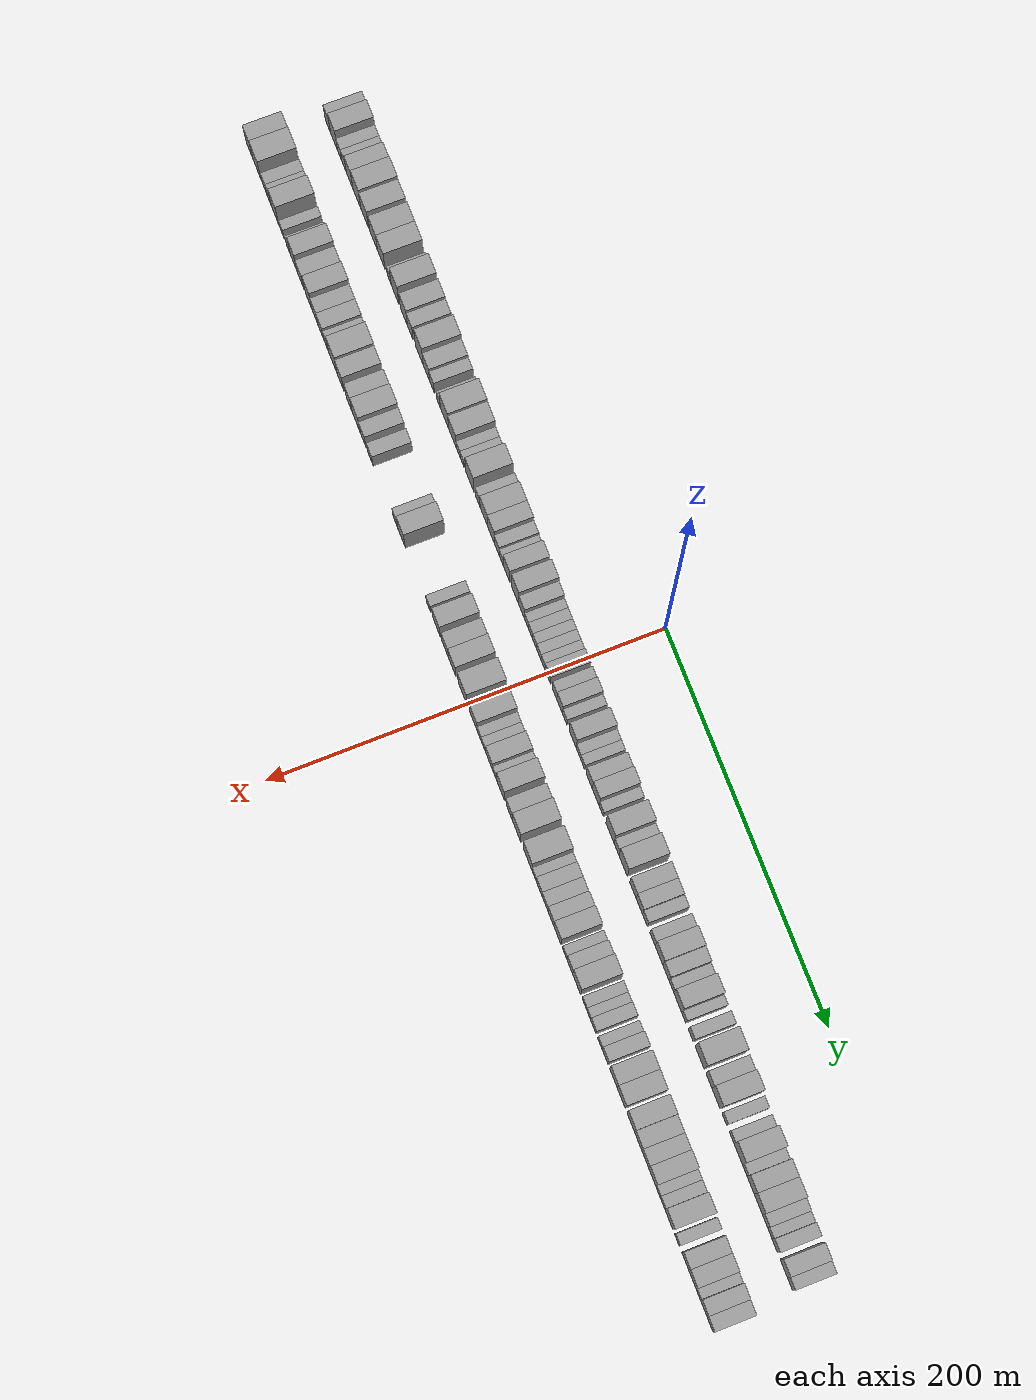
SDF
<sdf version="1.6">
 <world name="default">
  <scene>
   <sky><clouds><speed>12</speed></clouds></sky>
   <ambient>0.4 0.4 0.4 1</ambient>
   <background>0.7 0.7 0.7 1</background>
   <shadows>1</shadows>
  </scene>
  <gravity>0 0 -9.8066</gravity>
  <magnetic_field>6e-06 2.3e-05 -4.2e-05</magnetic_field>
  <physics default="0" name="default_physics" type="ode">
   <ode>
    <solver>
     <type>quick</type>
     <iters>10</iters>
     <sor>1.0</sor>
     <use_dynamic_moi_rescaling>0</use_dynamic_moi_rescaling>
    </solver>
    <constraints>
     <cfm>0</cfm>
     <erp>0.2</erp>
     <contact_max_correcting_vel>100</contact_max_correcting_vel>
     <contact_surface_layer>0.001</contact_surface_layer>
    </constraints>
   </ode>
   <max_step_size>0.004</max_step_size>
   <real_time_factor>1</real_time_factor>
   <real_time_update_rate>250</real_time_update_rate>
  </physics>
  <light name="sun" type="directional">
   <pose>0 0 10 0 0 0</pose>
   <diffuse>0.8 0.8 0.8 1</diffuse>
   <specular>0.2 0.2 0.2 1</specular>
   <attenuation>
    <range>1000</range>
    <constant>0.9</constant>
    <linear>0.01</linear>
    <quadratic>0.001</quadratic>
   </attenuation>
   <direction>-0.5 0.1 -0.9</direction>
  </light>
  <model name="building_1">
   <static>1</static>
   <pose>50.0000 -293.2844 0 0.000000 0.000000 0.000000</pose>
   <link name="link">
    <pose>0 0 9.00 0 0 0</pose>
    <collision name="collision"><geometry><box><size>20.0000 7.4312 18.0000</size></box></geometry></collision>
    <visual name="visual">
     <cast_shadows>0</cast_shadows>
     <geometry><box><size>20.0000 7.4312 18.0000</size></box></geometry>
     <material>
      <script>
       <uri>model://grey_wall/materials/scripts</uri>
       <uri>model://grey_wall/materials/textures</uri>
       <name>vrc/grey_wall</name>
      </script>
     </material>
    </visual>
   </link>
  </model>
  <model name="building_2">
   <static>1</static>
   <pose>50.0000 -284.7082 0 0.000000 0.000000 0.000000</pose>
   <link name="link">
    <pose>0 0 12.00 0 0 0</pose>
    <collision name="collision"><geometry><box><size>20.0000 9.7213 24.0000</size></box></geometry></collision>
    <visual name="visual">
     <cast_shadows>0</cast_shadows>
     <geometry><box><size>20.0000 9.7213 24.0000</size></box></geometry>
     <material>
      <script>
       <uri>model://grey_wall/materials/scripts</uri>
       <uri>model://grey_wall/materials/textures</uri>
       <name>vrc/grey_wall</name>
      </script>
     </material>
    </visual>
   </link>
  </model>
  <model name="building_3">
   <static>1</static>
   <pose>50.0000 -276.7827 0 0.000000 0.000000 0.000000</pose>
   <link name="link">
    <pose>0 0 7.50 0 0 0</pose>
    <collision name="collision"><geometry><box><size>20.0000 6.1296 15.0000</size></box></geometry></collision>
    <visual name="visual">
     <cast_shadows>0</cast_shadows>
     <geometry><box><size>20.0000 6.1296 15.0000</size></box></geometry>
     <material>
      <script>
       <uri>model://grey_wall/materials/scripts</uri>
       <uri>model://grey_wall/materials/textures</uri>
       <name>vrc/grey_wall</name>
      </script>
     </material>
    </visual>
   </link>
  </model>
  <model name="building_4">
   <static>1</static>
   <pose>50.0000 -270.6849 0 0.000000 0.000000 0.000000</pose>
   <link name="link">
    <pose>0 0 7.50 0 0 0</pose>
    <collision name="collision"><geometry><box><size>20.0000 6.0661 15.0000</size></box></geometry></collision>
    <visual name="visual">
     <cast_shadows>0</cast_shadows>
     <geometry><box><size>20.0000 6.0661 15.0000</size></box></geometry>
     <material>
      <script>
       <uri>model://grey_wall/materials/scripts</uri>
       <uri>model://grey_wall/materials/textures</uri>
       <name>vrc/grey_wall</name>
      </script>
     </material>
    </visual>
   </link>
  </model>
  <model name="building_5">
   <static>1</static>
   <pose>50.0000 -263.0242 0 0.000000 0.000000 0.000000</pose>
   <link name="link">
    <pose>0 0 10.50 0 0 0</pose>
    <collision name="collision"><geometry><box><size>20.0000 9.2553 21.0000</size></box></geometry></collision>
    <visual name="visual">
     <cast_shadows>0</cast_shadows>
     <geometry><box><size>20.0000 9.2553 21.0000</size></box></geometry>
     <material>
      <script>
       <uri>model://grey_wall/materials/scripts</uri>
       <uri>model://grey_wall/materials/textures</uri>
       <name>vrc/grey_wall</name>
      </script>
     </material>
    </visual>
   </link>
  </model>
  <model name="building_6">
   <static>1</static>
   <pose>50.0000 -252.9215 0 0.000000 0.000000 0.000000</pose>
   <link name="link">
    <pose>0 0 12.00 0 0 0</pose>
    <collision name="collision"><geometry><box><size>20.0000 10.9500 24.0000</size></box></geometry></collision>
    <visual name="visual">
     <cast_shadows>0</cast_shadows>
     <geometry><box><size>20.0000 10.9500 24.0000</size></box></geometry>
     <material>
      <script>
       <uri>model://grey_wall/materials/scripts</uri>
       <uri>model://grey_wall/materials/textures</uri>
       <name>vrc/grey_wall</name>
      </script>
     </material>
    </visual>
   </link>
  </model>
  <model name="building_7">
   <static>1</static>
   <pose>50.0000 -242.2019 0 0.000000 0.000000 0.000000</pose>
   <link name="link">
    <pose>0 0 10.50 0 0 0</pose>
    <collision name="collision"><geometry><box><size>20.0000 10.4893 21.0000</size></box></geometry></collision>
    <visual name="visual">
     <cast_shadows>0</cast_shadows>
     <geometry><box><size>20.0000 10.4893 21.0000</size></box></geometry>
     <material>
      <script>
       <uri>model://grey_wall/materials/scripts</uri>
       <uri>model://grey_wall/materials/textures</uri>
       <name>vrc/grey_wall</name>
      </script>
     </material>
    </visual>
   </link>
  </model>
  <model name="building_8">
   <static>1</static>
   <pose>50.0000 -229.7630 0 0.000000 0.000000 0.000000</pose>
   <link name="link">
    <pose>0 0 10.50 0 0 0</pose>
    <collision name="collision"><geometry><box><size>20.0000 10.3887 21.0000</size></box></geometry></collision>
    <visual name="visual">
     <cast_shadows>0</cast_shadows>
     <geometry><box><size>20.0000 10.3887 21.0000</size></box></geometry>
     <material>
      <script>
       <uri>model://grey_wall/materials/scripts</uri>
       <uri>model://grey_wall/materials/textures</uri>
       <name>vrc/grey_wall</name>
      </script>
     </material>
    </visual>
   </link>
  </model>
  <model name="building_9">
   <static>1</static>
   <pose>50.0000 -219.4591 0 0.000000 0.000000 0.000000</pose>
   <link name="link">
    <pose>0 0 10.50 0 0 0</pose>
    <collision name="collision"><geometry><box><size>20.0000 10.2190 21.0000</size></box></geometry></collision>
    <visual name="visual">
     <cast_shadows>0</cast_shadows>
     <geometry><box><size>20.0000 10.2190 21.0000</size></box></geometry>
     <material>
      <script>
       <uri>model://grey_wall/materials/scripts</uri>
       <uri>model://grey_wall/materials/textures</uri>
       <name>vrc/grey_wall</name>
      </script>
     </material>
    </visual>
   </link>
  </model>
  <model name="building_10">
   <static>1</static>
   <pose>50.0000 -208.5898 0 0.000000 0.000000 0.000000</pose>
   <link name="link">
    <pose>0 0 6.00 0 0 0</pose>
    <collision name="collision"><geometry><box><size>20.0000 5.5197 12.0000</size></box></geometry></collision>
    <visual name="visual">
     <cast_shadows>0</cast_shadows>
     <geometry><box><size>20.0000 5.5197 12.0000</size></box></geometry>
     <material>
      <script>
       <uri>model://grey_wall/materials/scripts</uri>
       <uri>model://grey_wall/materials/textures</uri>
       <name>vrc/grey_wall</name>
      </script>
     </material>
    </visual>
   </link>
  </model>
  <model name="building_11">
   <static>1</static>
   <pose>50.0000 -200.6034 0 0.000000 0.000000 0.000000</pose>
   <link name="link">
    <pose>0 0 12.00 0 0 0</pose>
    <collision name="collision"><geometry><box><size>20.0000 10.4530 24.0000</size></box></geometry></collision>
    <visual name="visual">
     <cast_shadows>0</cast_shadows>
     <geometry><box><size>20.0000 10.4530 24.0000</size></box></geometry>
     <material>
      <script>
       <uri>model://grey_wall/materials/scripts</uri>
       <uri>model://grey_wall/materials/textures</uri>
       <name>vrc/grey_wall</name>
      </script>
     </material>
    </visual>
   </link>
  </model>
  <model name="building_12">
   <static>1</static>
   <pose>50.0000 -188.6049 0 0.000000 0.000000 0.000000</pose>
   <link name="link">
    <pose>0 0 10.50 0 0 0</pose>
    <collision name="collision"><geometry><box><size>20.0000 9.5440 21.0000</size></box></geometry></collision>
    <visual name="visual">
     <cast_shadows>0</cast_shadows>
     <geometry><box><size>20.0000 9.5440 21.0000</size></box></geometry>
     <material>
      <script>
       <uri>model://grey_wall/materials/scripts</uri>
       <uri>model://grey_wall/materials/textures</uri>
       <name>vrc/grey_wall</name>
      </script>
     </material>
    </visual>
   </link>
  </model>
  <model name="building_13">
   <static>1</static>
   <pose>50.0000 -179.9574 0 0.000000 0.000000 0.000000</pose>
   <link name="link">
    <pose>0 0 9.00 0 0 0</pose>
    <collision name="collision"><geometry><box><size>20.0000 7.7511 18.0000</size></box></geometry></collision>
    <visual name="visual">
     <cast_shadows>0</cast_shadows>
     <geometry><box><size>20.0000 7.7511 18.0000</size></box></geometry>
     <material>
      <script>
       <uri>model://grey_wall/materials/scripts</uri>
       <uri>model://grey_wall/materials/textures</uri>
       <name>vrc/grey_wall</name>
      </script>
     </material>
    </visual>
   </link>
  </model>
  <model name="building_14">
   <static>1</static>
   <pose>50.0000 -167.8056 0 0.000000 0.000000 0.000000</pose>
   <link name="link">
    <pose>0 0 12.00 0 0 0</pose>
    <collision name="collision"><geometry><box><size>20.0000 10.5525 24.0000</size></box></geometry></collision>
    <visual name="visual">
     <cast_shadows>0</cast_shadows>
     <geometry><box><size>20.0000 10.5525 24.0000</size></box></geometry>
     <material>
      <script>
       <uri>model://grey_wall/materials/scripts</uri>
       <uri>model://grey_wall/materials/textures</uri>
       <name>vrc/grey_wall</name>
      </script>
     </material>
    </visual>
   </link>
  </model>
  <model name="building_15">
   <static>1</static>
   <pose>50.0000 -158.1471 0 0.000000 0.000000 0.000000</pose>
   <link name="link">
    <pose>0 0 9.00 0 0 0</pose>
    <collision name="collision"><geometry><box><size>20.0000 8.7645 18.0000</size></box></geometry></collision>
    <visual name="visual">
     <cast_shadows>0</cast_shadows>
     <geometry><box><size>20.0000 8.7645 18.0000</size></box></geometry>
     <material>
      <script>
       <uri>model://grey_wall/materials/scripts</uri>
       <uri>model://grey_wall/materials/textures</uri>
       <name>vrc/grey_wall</name>
      </script>
     </material>
    </visual>
   </link>
  </model>
  <model name="building_16">
   <static>1</static>
   <pose>50.0000 -150.6009 0 0.000000 0.000000 0.000000</pose>
   <link name="link">
    <pose>0 0 7.50 0 0 0</pose>
    <collision name="collision"><geometry><box><size>20.0000 6.3280 15.0000</size></box></geometry></collision>
    <visual name="visual">
     <cast_shadows>0</cast_shadows>
     <geometry><box><size>20.0000 6.3280 15.0000</size></box></geometry>
     <material>
      <script>
       <uri>model://grey_wall/materials/scripts</uri>
       <uri>model://grey_wall/materials/textures</uri>
       <name>vrc/grey_wall</name>
      </script>
     </material>
    </visual>
   </link>
  </model>
  <model name="building_17">
   <static>1</static>
   <pose>50.0000 -141.9502 0 0.000000 0.000000 0.000000</pose>
   <link name="link">
    <pose>0 0 6.00 0 0 0</pose>
    <collision name="collision"><geometry><box><size>20.0000 4.9733 12.0000</size></box></geometry></collision>
    <visual name="visual">
     <cast_shadows>0</cast_shadows>
     <geometry><box><size>20.0000 4.9733 12.0000</size></box></geometry>
     <material>
      <script>
       <uri>model://grey_wall/materials/scripts</uri>
       <uri>model://grey_wall/materials/textures</uri>
       <name>vrc/grey_wall</name>
      </script>
     </material>
    </visual>
   </link>
  </model>
  <model name="building_18">
   <static>1</static>
   <pose>50.0000 -133.9156 0 0.000000 0.000000 0.000000</pose>
   <link name="link">
    <pose>0 0 12.00 0 0 0</pose>
    <collision name="collision"><geometry><box><size>20.0000 11.0959 24.0000</size></box></geometry></collision>
    <visual name="visual">
     <cast_shadows>0</cast_shadows>
     <geometry><box><size>20.0000 11.0959 24.0000</size></box></geometry>
     <material>
      <script>
       <uri>model://grey_wall/materials/scripts</uri>
       <uri>model://grey_wall/materials/textures</uri>
       <name>vrc/grey_wall</name>
      </script>
     </material>
    </visual>
   </link>
  </model>
  <model name="building_19">
   <static>1</static>
   <pose>50.0000 -123.1510 0 0.000000 0.000000 0.000000</pose>
   <link name="link">
    <pose>0 0 10.50 0 0 0</pose>
    <collision name="collision"><geometry><box><size>20.0000 10.4332 21.0000</size></box></geometry></collision>
    <visual name="visual">
     <cast_shadows>0</cast_shadows>
     <geometry><box><size>20.0000 10.4332 21.0000</size></box></geometry>
     <material>
      <script>
       <uri>model://grey_wall/materials/scripts</uri>
       <uri>model://grey_wall/materials/textures</uri>
       <name>vrc/grey_wall</name>
      </script>
     </material>
    </visual>
   </link>
  </model>
  <model name="building_20">
   <static>1</static>
   <pose>50.0000 -115.3216 0 0.000000 0.000000 0.000000</pose>
   <link name="link">
    <pose>0 0 6.00 0 0 0</pose>
    <collision name="collision"><geometry><box><size>20.0000 5.2257 12.0000</size></box></geometry></collision>
    <visual name="visual">
     <cast_shadows>0</cast_shadows>
     <geometry><box><size>20.0000 5.2257 12.0000</size></box></geometry>
     <material>
      <script>
       <uri>model://grey_wall/materials/scripts</uri>
       <uri>model://grey_wall/materials/textures</uri>
       <name>vrc/grey_wall</name>
      </script>
     </material>
    </visual>
   </link>
  </model>
  <model name="building_21">
   <static>1</static>
   <pose>50.0000 -110.1633 0 0.000000 0.000000 0.000000</pose>
   <link name="link">
    <pose>0 0 6.00 0 0 0</pose>
    <collision name="collision"><geometry><box><size>20.0000 5.0907 12.0000</size></box></geometry></collision>
    <visual name="visual">
     <cast_shadows>0</cast_shadows>
     <geometry><box><size>20.0000 5.0907 12.0000</size></box></geometry>
     <material>
      <script>
       <uri>model://grey_wall/materials/scripts</uri>
       <uri>model://grey_wall/materials/textures</uri>
       <name>vrc/grey_wall</name>
      </script>
     </material>
    </visual>
   </link>
  </model>
  <model name="building_22">
   <static>1</static>
   <pose>50.0000 -100.2157 0 0.000000 0.000000 0.000000</pose>
   <link name="link">
    <pose>0 0 12.00 0 0 0</pose>
    <collision name="collision"><geometry><box><size>20.0000 10.8044 24.0000</size></box></geometry></collision>
    <visual name="visual">
     <cast_shadows>0</cast_shadows>
     <geometry><box><size>20.0000 10.8044 24.0000</size></box></geometry>
     <material>
      <script>
       <uri>model://grey_wall/materials/scripts</uri>
       <uri>model://grey_wall/materials/textures</uri>
       <name>vrc/grey_wall</name>
      </script>
     </material>
    </visual>
   </link>
  </model>
  <model name="building_23">
   <static>1</static>
   <pose>50.0000 -89.7036 0 0.000000 0.000000 0.000000</pose>
   <link name="link">
    <pose>0 0 7.50 0 0 0</pose>
    <collision name="collision"><geometry><box><size>20.0000 6.2199 15.0000</size></box></geometry></collision>
    <visual name="visual">
     <cast_shadows>0</cast_shadows>
     <geometry><box><size>20.0000 6.2199 15.0000</size></box></geometry>
     <material>
      <script>
       <uri>model://grey_wall/materials/scripts</uri>
       <uri>model://grey_wall/materials/textures</uri>
       <name>vrc/grey_wall</name>
      </script>
     </material>
    </visual>
   </link>
  </model>
  <model name="building_24">
   <static>1</static>
   <pose>50.0000 -81.5921 0 0.000000 0.000000 0.000000</pose>
   <link name="link">
    <pose>0 0 10.50 0 0 0</pose>
    <collision name="collision"><geometry><box><size>20.0000 10.0030 21.0000</size></box></geometry></collision>
    <visual name="visual">
     <cast_shadows>0</cast_shadows>
     <geometry><box><size>20.0000 10.0030 21.0000</size></box></geometry>
     <material>
      <script>
       <uri>model://grey_wall/materials/scripts</uri>
       <uri>model://grey_wall/materials/textures</uri>
       <name>vrc/grey_wall</name>
      </script>
     </material>
    </visual>
   </link>
  </model>
  <model name="building_25">
   <static>1</static>
   <pose>50.0000 -72.2577 0 0.000000 0.000000 0.000000</pose>
   <link name="link">
    <pose>0 0 10.50 0 0 0</pose>
    <collision name="collision"><geometry><box><size>20.0000 8.6659 21.0000</size></box></geometry></collision>
    <visual name="visual">
     <cast_shadows>0</cast_shadows>
     <geometry><box><size>20.0000 8.6659 21.0000</size></box></geometry>
     <material>
      <script>
       <uri>model://grey_wall/materials/scripts</uri>
       <uri>model://grey_wall/materials/textures</uri>
       <name>vrc/grey_wall</name>
      </script>
     </material>
    </visual>
   </link>
  </model>
  <model name="building_26">
   <static>1</static>
   <pose>50.0000 -64.6622 0 0.000000 0.000000 0.000000</pose>
   <link name="link">
    <pose>0 0 7.50 0 0 0</pose>
    <collision name="collision"><geometry><box><size>20.0000 6.5250 15.0000</size></box></geometry></collision>
    <visual name="visual">
     <cast_shadows>0</cast_shadows>
     <geometry><box><size>20.0000 6.5250 15.0000</size></box></geometry>
     <material>
      <script>
       <uri>model://grey_wall/materials/scripts</uri>
       <uri>model://grey_wall/materials/textures</uri>
       <name>vrc/grey_wall</name>
      </script>
     </material>
    </visual>
   </link>
  </model>
  <model name="building_27">
   <static>1</static>
   <pose>50.0000 -58.7691 0 0.000000 0.000000 0.000000</pose>
   <link name="link">
    <pose>0 0 6.00 0 0 0</pose>
    <collision name="collision"><geometry><box><size>20.0000 5.2613 12.0000</size></box></geometry></collision>
    <visual name="visual">
     <cast_shadows>0</cast_shadows>
     <geometry><box><size>20.0000 5.2613 12.0000</size></box></geometry>
     <material>
      <script>
       <uri>model://grey_wall/materials/scripts</uri>
       <uri>model://grey_wall/materials/textures</uri>
       <name>vrc/grey_wall</name>
      </script>
     </material>
    </visual>
   </link>
  </model>
  <model name="building_28">
   <static>1</static>
   <pose>50.0000 -51.8409 0 0.000000 0.000000 0.000000</pose>
   <link name="link">
    <pose>0 0 10.50 0 0 0</pose>
    <collision name="collision"><geometry><box><size>20.0000 8.5952 21.0000</size></box></geometry></collision>
    <visual name="visual">
     <cast_shadows>0</cast_shadows>
     <geometry><box><size>20.0000 8.5952 21.0000</size></box></geometry>
     <material>
      <script>
       <uri>model://grey_wall/materials/scripts</uri>
       <uri>model://grey_wall/materials/textures</uri>
       <name>vrc/grey_wall</name>
      </script>
     </material>
    </visual>
   </link>
  </model>
  <model name="building_29">
   <static>1</static>
   <pose>50.0000 -40.7282 0 0.000000 0.000000 0.000000</pose>
   <link name="link">
    <pose>0 0 12.00 0 0 0</pose>
    <collision name="collision"><geometry><box><size>20.0000 9.6301 24.0000</size></box></geometry></collision>
    <visual name="visual">
     <cast_shadows>0</cast_shadows>
     <geometry><box><size>20.0000 9.6301 24.0000</size></box></geometry>
     <material>
      <script>
       <uri>model://grey_wall/materials/scripts</uri>
       <uri>model://grey_wall/materials/textures</uri>
       <name>vrc/grey_wall</name>
      </script>
     </material>
    </visual>
   </link>
  </model>
  <model name="building_30">
   <static>1</static>
   <pose>50.0000 -32.2528 0 0.000000 0.000000 0.000000</pose>
   <link name="link">
    <pose>0 0 9.00 0 0 0</pose>
    <collision name="collision"><geometry><box><size>20.0000 7.3209 18.0000</size></box></geometry></collision>
    <visual name="visual">
     <cast_shadows>0</cast_shadows>
     <geometry><box><size>20.0000 7.3209 18.0000</size></box></geometry>
     <material>
      <script>
       <uri>model://grey_wall/materials/scripts</uri>
       <uri>model://grey_wall/materials/textures</uri>
       <name>vrc/grey_wall</name>
      </script>
     </material>
    </visual>
   </link>
  </model>
  <model name="building_31">
   <static>1</static>
   <pose>50.0000 -26.1477 0 0.000000 0.000000 0.000000</pose>
   <link name="link">
    <pose>0 0 6.00 0 0 0</pose>
    <collision name="collision"><geometry><box><size>20.0000 4.8893 12.0000</size></box></geometry></collision>
    <visual name="visual">
     <cast_shadows>0</cast_shadows>
     <geometry><box><size>20.0000 4.8893 12.0000</size></box></geometry>
     <material>
      <script>
       <uri>model://grey_wall/materials/scripts</uri>
       <uri>model://grey_wall/materials/textures</uri>
       <name>vrc/grey_wall</name>
      </script>
     </material>
    </visual>
   </link>
  </model>
  <model name="building_32">
   <static>1</static>
   <pose>50.0000 -20.8695 0 0.000000 0.000000 0.000000</pose>
   <link name="link">
    <pose>0 0 6.00 0 0 0</pose>
    <collision name="collision"><geometry><box><size>20.0000 5.6669 12.0000</size></box></geometry></collision>
    <visual name="visual">
     <cast_shadows>0</cast_shadows>
     <geometry><box><size>20.0000 5.6669 12.0000</size></box></geometry>
     <material>
      <script>
       <uri>model://grey_wall/materials/scripts</uri>
       <uri>model://grey_wall/materials/textures</uri>
       <name>vrc/grey_wall</name>
      </script>
     </material>
    </visual>
   </link>
  </model>
  <model name="building_33">
   <static>1</static>
   <pose>50.0000 -15.4163 0 0.000000 0.000000 0.000000</pose>
   <link name="link">
    <pose>0 0 6.00 0 0 0</pose>
    <collision name="collision"><geometry><box><size>20.0000 5.2396 12.0000</size></box></geometry></collision>
    <visual name="visual">
     <cast_shadows>0</cast_shadows>
     <geometry><box><size>20.0000 5.2396 12.0000</size></box></geometry>
     <material>
      <script>
       <uri>model://grey_wall/materials/scripts</uri>
       <uri>model://grey_wall/materials/textures</uri>
       <name>vrc/grey_wall</name>
      </script>
     </material>
    </visual>
   </link>
  </model>
  <model name="building_34">
   <static>1</static>
   <pose>50.0000 -10.0807 0 0.000000 0.000000 0.000000</pose>
   <link name="link">
    <pose>0 0 6.00 0 0 0</pose>
    <collision name="collision"><geometry><box><size>20.0000 5.4316 12.0000</size></box></geometry></collision>
    <visual name="visual">
     <cast_shadows>0</cast_shadows>
     <geometry><box><size>20.0000 5.4316 12.0000</size></box></geometry>
     <material>
      <script>
       <uri>model://grey_wall/materials/scripts</uri>
       <uri>model://grey_wall/materials/textures</uri>
       <name>vrc/grey_wall</name>
      </script>
     </material>
    </visual>
   </link>
  </model>
  <model name="building_35">
   <static>1</static>
   <pose>50.0000 -4.8146 0 0.000000 0.000000 0.000000</pose>
   <link name="link">
    <pose>0 0 6.00 0 0 0</pose>
    <collision name="collision"><geometry><box><size>20.0000 5.1007 12.0000</size></box></geometry></collision>
    <visual name="visual">
     <cast_shadows>0</cast_shadows>
     <geometry><box><size>20.0000 5.1007 12.0000</size></box></geometry>
     <material>
      <script>
       <uri>model://grey_wall/materials/scripts</uri>
       <uri>model://grey_wall/materials/textures</uri>
       <name>vrc/grey_wall</name>
      </script>
     </material>
    </visual>
   </link>
  </model>
  <model name="building_36">
   <static>1</static>
   <pose>50.0000 1.3412 0 0.000000 0.000000 0.000000</pose>
   <link name="link">
    <pose>0 0 7.50 0 0 0</pose>
    <collision name="collision"><geometry><box><size>20.0000 7.2109 15.0000</size></box></geometry></collision>
    <visual name="visual">
     <cast_shadows>0</cast_shadows>
     <geometry><box><size>20.0000 7.2109 15.0000</size></box></geometry>
     <material>
      <script>
       <uri>model://grey_wall/materials/scripts</uri>
       <uri>model://grey_wall/materials/textures</uri>
       <name>vrc/grey_wall</name>
      </script>
     </material>
    </visual>
   </link>
  </model>
  <model name="building_37">
   <static>1</static>
   <pose>50.0000 9.9904 0 0.000000 0.000000 0.000000</pose>
   <link name="link">
    <pose>0 0 7.50 0 0 0</pose>
    <collision name="collision"><geometry><box><size>20.0000 6.0876 15.0000</size></box></geometry></collision>
    <visual name="visual">
     <cast_shadows>0</cast_shadows>
     <geometry><box><size>20.0000 6.0876 15.0000</size></box></geometry>
     <material>
      <script>
       <uri>model://grey_wall/materials/scripts</uri>
       <uri>model://grey_wall/materials/textures</uri>
       <name>vrc/grey_wall</name>
      </script>
     </material>
    </visual>
   </link>
  </model>
  <model name="building_38">
   <static>1</static>
   <pose>50.0000 16.7120 0 0.000000 0.000000 0.000000</pose>
   <link name="link">
    <pose>0 0 9.00 0 0 0</pose>
    <collision name="collision"><geometry><box><size>20.0000 7.3554 18.0000</size></box></geometry></collision>
    <visual name="visual">
     <cast_shadows>0</cast_shadows>
     <geometry><box><size>20.0000 7.3554 18.0000</size></box></geometry>
     <material>
      <script>
       <uri>model://grey_wall/materials/scripts</uri>
       <uri>model://grey_wall/materials/textures</uri>
       <name>vrc/grey_wall</name>
      </script>
     </material>
    </visual>
   </link>
  </model>
  <model name="building_39">
   <static>1</static>
   <pose>50.0000 23.1446 0 0.000000 0.000000 0.000000</pose>
   <link name="link">
    <pose>0 0 6.00 0 0 0</pose>
    <collision name="collision"><geometry><box><size>20.0000 5.5098 12.0000</size></box></geometry></collision>
    <visual name="visual">
     <cast_shadows>0</cast_shadows>
     <geometry><box><size>20.0000 5.5098 12.0000</size></box></geometry>
     <material>
      <script>
       <uri>model://grey_wall/materials/scripts</uri>
       <uri>model://grey_wall/materials/textures</uri>
       <name>vrc/grey_wall</name>
      </script>
     </material>
    </visual>
   </link>
  </model>
  <model name="building_40">
   <static>1</static>
   <pose>50.0000 33.3814 0 0.000000 0.000000 0.000000</pose>
   <link name="link">
    <pose>0 0 10.50 0 0 0</pose>
    <collision name="collision"><geometry><box><size>20.0000 8.9638 21.0000</size></box></geometry></collision>
    <visual name="visual">
     <cast_shadows>0</cast_shadows>
     <geometry><box><size>20.0000 8.9638 21.0000</size></box></geometry>
     <material>
      <script>
       <uri>model://grey_wall/materials/scripts</uri>
       <uri>model://grey_wall/materials/textures</uri>
       <name>vrc/grey_wall</name>
      </script>
     </material>
    </visual>
   </link>
  </model>
  <model name="building_41">
   <static>1</static>
   <pose>50.0000 40.6483 0 0.000000 0.000000 0.000000</pose>
   <link name="link">
    <pose>0 0 6.00 0 0 0</pose>
    <collision name="collision"><geometry><box><size>20.0000 5.5700 12.0000</size></box></geometry></collision>
    <visual name="visual">
     <cast_shadows>0</cast_shadows>
     <geometry><box><size>20.0000 5.5700 12.0000</size></box></geometry>
     <material>
      <script>
       <uri>model://grey_wall/materials/scripts</uri>
       <uri>model://grey_wall/materials/textures</uri>
       <name>vrc/grey_wall</name>
      </script>
     </material>
    </visual>
   </link>
  </model>
  <model name="building_42">
   <static>1</static>
   <pose>50.0000 46.0547 0 0.000000 0.000000 0.000000</pose>
   <link name="link">
    <pose>0 0 6.00 0 0 0</pose>
    <collision name="collision"><geometry><box><size>20.0000 5.2428 12.0000</size></box></geometry></collision>
    <visual name="visual">
     <cast_shadows>0</cast_shadows>
     <geometry><box><size>20.0000 5.2428 12.0000</size></box></geometry>
     <material>
      <script>
       <uri>model://grey_wall/materials/scripts</uri>
       <uri>model://grey_wall/materials/textures</uri>
       <name>vrc/grey_wall</name>
      </script>
     </material>
    </visual>
   </link>
  </model>
  <model name="building_43">
   <static>1</static>
   <pose>50.0000 54.5110 0 0.000000 0.000000 0.000000</pose>
   <link name="link">
    <pose>0 0 9.00 0 0 0</pose>
    <collision name="collision"><geometry><box><size>20.0000 7.6698 18.0000</size></box></geometry></collision>
    <visual name="visual">
     <cast_shadows>0</cast_shadows>
     <geometry><box><size>20.0000 7.6698 18.0000</size></box></geometry>
     <material>
      <script>
       <uri>model://grey_wall/materials/scripts</uri>
       <uri>model://grey_wall/materials/textures</uri>
       <name>vrc/grey_wall</name>
      </script>
     </material>
    </visual>
   </link>
  </model>
  <model name="building_44">
   <static>1</static>
   <pose>50.0000 62.5770 0 0.000000 0.000000 0.000000</pose>
   <link name="link">
    <pose>0 0 10.50 0 0 0</pose>
    <collision name="collision"><geometry><box><size>20.0000 8.4621 21.0000</size></box></geometry></collision>
    <visual name="visual">
     <cast_shadows>0</cast_shadows>
     <geometry><box><size>20.0000 8.4621 21.0000</size></box></geometry>
     <material>
      <script>
       <uri>model://grey_wall/materials/scripts</uri>
       <uri>model://grey_wall/materials/textures</uri>
       <name>vrc/grey_wall</name>
      </script>
     </material>
    </visual>
   </link>
  </model>
  <model name="building_45">
   <static>1</static>
   <pose>50.0000 69.5375 0 0.000000 0.000000 0.000000</pose>
   <link name="link">
    <pose>0 0 6.00 0 0 0</pose>
    <collision name="collision"><geometry><box><size>20.0000 5.4590 12.0000</size></box></geometry></collision>
    <visual name="visual">
     <cast_shadows>0</cast_shadows>
     <geometry><box><size>20.0000 5.4590 12.0000</size></box></geometry>
     <material>
      <script>
       <uri>model://grey_wall/materials/scripts</uri>
       <uri>model://grey_wall/materials/textures</uri>
       <name>vrc/grey_wall</name>
      </script>
     </material>
    </visual>
   </link>
  </model>
  <model name="building_46">
   <static>1</static>
   <pose>50.0000 80.4547 0 0.000000 0.000000 0.000000</pose>
   <link name="link">
    <pose>0 0 12.00 0 0 0</pose>
    <collision name="collision"><geometry><box><size>20.0000 10.3753 24.0000</size></box></geometry></collision>
    <visual name="visual">
     <cast_shadows>0</cast_shadows>
     <geometry><box><size>20.0000 10.3753 24.0000</size></box></geometry>
     <material>
      <script>
       <uri>model://grey_wall/materials/scripts</uri>
       <uri>model://grey_wall/materials/textures</uri>
       <name>vrc/grey_wall</name>
      </script>
     </material>
    </visual>
   </link>
  </model>
  <model name="building_47">
   <static>1</static>
   <pose>50.0000 88.7172 0 0.000000 0.000000 0.000000</pose>
   <link name="link">
    <pose>0 0 7.50 0 0 0</pose>
    <collision name="collision"><geometry><box><size>20.0000 6.1498 15.0000</size></box></geometry></collision>
    <visual name="visual">
     <cast_shadows>0</cast_shadows>
     <geometry><box><size>20.0000 6.1498 15.0000</size></box></geometry>
     <material>
      <script>
       <uri>model://grey_wall/materials/scripts</uri>
       <uri>model://grey_wall/materials/textures</uri>
       <name>vrc/grey_wall</name>
      </script>
     </material>
    </visual>
   </link>
  </model>
  <model name="building_48">
   <static>1</static>
   <pose>50.0000 96.9360 0 0.000000 0.000000 0.000000</pose>
   <link name="link">
    <pose>0 0 12.00 0 0 0</pose>
    <collision name="collision"><geometry><box><size>20.0000 10.2880 24.0000</size></box></geometry></collision>
    <visual name="visual">
     <cast_shadows>0</cast_shadows>
     <geometry><box><size>20.0000 10.2880 24.0000</size></box></geometry>
     <material>
      <script>
       <uri>model://grey_wall/materials/scripts</uri>
       <uri>model://grey_wall/materials/textures</uri>
       <name>vrc/grey_wall</name>
      </script>
     </material>
    </visual>
   </link>
  </model>
  <model name="building_49">
   <static>1</static>
   <pose>50.0000 109.0891 0 0.000000 0.000000 0.000000</pose>
   <link name="link">
    <pose>0 0 9.00 0 0 0</pose>
    <collision name="collision"><geometry><box><size>20.0000 8.0180 18.0000</size></box></geometry></collision>
    <visual name="visual">
     <cast_shadows>0</cast_shadows>
     <geometry><box><size>20.0000 8.0180 18.0000</size></box></geometry>
     <material>
      <script>
       <uri>model://grey_wall/materials/scripts</uri>
       <uri>model://grey_wall/materials/textures</uri>
       <name>vrc/grey_wall</name>
      </script>
     </material>
    </visual>
   </link>
  </model>
  <model name="building_50">
   <static>1</static>
   <pose>50.0000 117.0477 0 0.000000 0.000000 0.000000</pose>
   <link name="link">
    <pose>0 0 9.00 0 0 0</pose>
    <collision name="collision"><geometry><box><size>20.0000 7.8993 18.0000</size></box></geometry></collision>
    <visual name="visual">
     <cast_shadows>0</cast_shadows>
     <geometry><box><size>20.0000 7.8993 18.0000</size></box></geometry>
     <material>
      <script>
       <uri>model://grey_wall/materials/scripts</uri>
       <uri>model://grey_wall/materials/textures</uri>
       <name>vrc/grey_wall</name>
      </script>
     </material>
    </visual>
   </link>
  </model>
  <model name="building_51">
   <static>1</static>
   <pose>50.0000 124.0484 0 0.000000 0.000000 0.000000</pose>
   <link name="link">
    <pose>0 0 7.50 0 0 0</pose>
    <collision name="collision"><geometry><box><size>20.0000 6.1020 15.0000</size></box></geometry></collision>
    <visual name="visual">
     <cast_shadows>0</cast_shadows>
     <geometry><box><size>20.0000 6.1020 15.0000</size></box></geometry>
     <material>
      <script>
       <uri>model://grey_wall/materials/scripts</uri>
       <uri>model://grey_wall/materials/textures</uri>
       <name>vrc/grey_wall</name>
      </script>
     </material>
    </visual>
   </link>
  </model>
  <model name="building_52">
   <static>1</static>
   <pose>50.0000 133.3805 0 0.000000 0.000000 0.000000</pose>
   <link name="link">
    <pose>0 0 7.50 0 0 0</pose>
    <collision name="collision"><geometry><box><size>20.0000 6.5623 15.0000</size></box></geometry></collision>
    <visual name="visual">
     <cast_shadows>0</cast_shadows>
     <geometry><box><size>20.0000 6.5623 15.0000</size></box></geometry>
     <material>
      <script>
       <uri>model://grey_wall/materials/scripts</uri>
       <uri>model://grey_wall/materials/textures</uri>
       <name>vrc/grey_wall</name>
      </script>
     </material>
    </visual>
   </link>
  </model>
  <model name="building_53">
   <static>1</static>
   <pose>50.0000 141.4702 0 0.000000 0.000000 0.000000</pose>
   <link name="link">
    <pose>0 0 10.50 0 0 0</pose>
    <collision name="collision"><geometry><box><size>20.0000 9.6170 21.0000</size></box></geometry></collision>
    <visual name="visual">
     <cast_shadows>0</cast_shadows>
     <geometry><box><size>20.0000 9.6170 21.0000</size></box></geometry>
     <material>
      <script>
       <uri>model://grey_wall/materials/scripts</uri>
       <uri>model://grey_wall/materials/textures</uri>
       <name>vrc/grey_wall</name>
      </script>
     </material>
    </visual>
   </link>
  </model>
  <model name="building_54">
   <static>1</static>
   <pose>50.0000 150.0559 0 0.000000 0.000000 0.000000</pose>
   <link name="link">
    <pose>0 0 9.00 0 0 0</pose>
    <collision name="collision"><geometry><box><size>20.0000 7.5544 18.0000</size></box></geometry></collision>
    <visual name="visual">
     <cast_shadows>0</cast_shadows>
     <geometry><box><size>20.0000 7.5544 18.0000</size></box></geometry>
     <material>
      <script>
       <uri>model://grey_wall/materials/scripts</uri>
       <uri>model://grey_wall/materials/textures</uri>
       <name>vrc/grey_wall</name>
      </script>
     </material>
    </visual>
   </link>
  </model>
  <model name="building_55">
   <static>1</static>
   <pose>50.0000 156.7606 0 0.000000 0.000000 0.000000</pose>
   <link name="link">
    <pose>0 0 6.00 0 0 0</pose>
    <collision name="collision"><geometry><box><size>20.0000 5.8550 12.0000</size></box></geometry></collision>
    <visual name="visual">
     <cast_shadows>0</cast_shadows>
     <geometry><box><size>20.0000 5.8550 12.0000</size></box></geometry>
     <material>
      <script>
       <uri>model://grey_wall/materials/scripts</uri>
       <uri>model://grey_wall/materials/textures</uri>
       <name>vrc/grey_wall</name>
      </script>
     </material>
    </visual>
   </link>
  </model>
  <model name="building_56">
   <static>1</static>
   <pose>50.0000 164.5068 0 0.000000 0.000000 0.000000</pose>
   <link name="link">
    <pose>0 0 10.50 0 0 0</pose>
    <collision name="collision"><geometry><box><size>20.0000 9.6375 21.0000</size></box></geometry></collision>
    <visual name="visual">
     <cast_shadows>0</cast_shadows>
     <geometry><box><size>20.0000 9.6375 21.0000</size></box></geometry>
     <material>
      <script>
       <uri>model://grey_wall/materials/scripts</uri>
       <uri>model://grey_wall/materials/textures</uri>
       <name>vrc/grey_wall</name>
      </script>
     </material>
    </visual>
   </link>
  </model>
  <model name="building_57">
   <static>1</static>
   <pose>50.0000 171.8528 0 0.000000 0.000000 0.000000</pose>
   <link name="link">
    <pose>0 0 6.00 0 0 0</pose>
    <collision name="collision"><geometry><box><size>20.0000 5.0544 12.0000</size></box></geometry></collision>
    <visual name="visual">
     <cast_shadows>0</cast_shadows>
     <geometry><box><size>20.0000 5.0544 12.0000</size></box></geometry>
     <material>
      <script>
       <uri>model://grey_wall/materials/scripts</uri>
       <uri>model://grey_wall/materials/textures</uri>
       <name>vrc/grey_wall</name>
      </script>
     </material>
    </visual>
   </link>
  </model>
  <model name="building_58">
   <static>1</static>
   <pose>50.0000 180.4692 0 0.000000 0.000000 0.000000</pose>
   <link name="link">
    <pose>0 0 7.50 0 0 0</pose>
    <collision name="collision"><geometry><box><size>20.0000 6.1785 15.0000</size></box></geometry></collision>
    <visual name="visual">
     <cast_shadows>0</cast_shadows>
     <geometry><box><size>20.0000 6.1785 15.0000</size></box></geometry>
     <material>
      <script>
       <uri>model://grey_wall/materials/scripts</uri>
       <uri>model://grey_wall/materials/textures</uri>
       <name>vrc/grey_wall</name>
      </script>
     </material>
    </visual>
   </link>
  </model>
  <model name="building_59">
   <static>1</static>
   <pose>50.0000 191.1664 0 0.000000 0.000000 0.000000</pose>
   <link name="link">
    <pose>0 0 12.00 0 0 0</pose>
    <collision name="collision"><geometry><box><size>20.0000 11.2157 24.0000</size></box></geometry></collision>
    <visual name="visual">
     <cast_shadows>0</cast_shadows>
     <geometry><box><size>20.0000 11.2157 24.0000</size></box></geometry>
     <material>
      <script>
       <uri>model://grey_wall/materials/scripts</uri>
       <uri>model://grey_wall/materials/textures</uri>
       <name>vrc/grey_wall</name>
      </script>
     </material>
    </visual>
   </link>
  </model>
  <model name="building_60">
   <static>1</static>
   <pose>50.0000 202.4280 0 0.000000 0.000000 0.000000</pose>
   <link name="link">
    <pose>0 0 9.00 0 0 0</pose>
    <collision name="collision"><geometry><box><size>20.0000 7.3075 18.0000</size></box></geometry></collision>
    <visual name="visual">
     <cast_shadows>0</cast_shadows>
     <geometry><box><size>20.0000 7.3075 18.0000</size></box></geometry>
     <material>
      <script>
       <uri>model://grey_wall/materials/scripts</uri>
       <uri>model://grey_wall/materials/textures</uri>
       <name>vrc/grey_wall</name>
      </script>
     </material>
    </visual>
   </link>
  </model>
  <model name="building_61">
   <static>1</static>
   <pose>50.0000 211.0458 0 0.000000 0.000000 0.000000</pose>
   <link name="link">
    <pose>0 0 12.00 0 0 0</pose>
    <collision name="collision"><geometry><box><size>20.0000 9.9281 24.0000</size></box></geometry></collision>
    <visual name="visual">
     <cast_shadows>0</cast_shadows>
     <geometry><box><size>20.0000 9.9281 24.0000</size></box></geometry>
     <material>
      <script>
       <uri>model://grey_wall/materials/scripts</uri>
       <uri>model://grey_wall/materials/textures</uri>
       <name>vrc/grey_wall</name>
      </script>
     </material>
    </visual>
   </link>
  </model>
  <model name="building_62">
   <static>1</static>
   <pose>50.0000 220.9397 0 0.000000 0.000000 0.000000</pose>
   <link name="link">
    <pose>0 0 6.00 0 0 0</pose>
    <collision name="collision"><geometry><box><size>20.0000 5.8596 12.0000</size></box></geometry></collision>
    <visual name="visual">
     <cast_shadows>0</cast_shadows>
     <geometry><box><size>20.0000 5.8596 12.0000</size></box></geometry>
     <material>
      <script>
       <uri>model://grey_wall/materials/scripts</uri>
       <uri>model://grey_wall/materials/textures</uri>
       <name>vrc/grey_wall</name>
      </script>
     </material>
    </visual>
   </link>
  </model>
  <model name="building_63">
   <static>1</static>
   <pose>50.0000 229.6575 0 0.000000 0.000000 0.000000</pose>
   <link name="link">
    <pose>0 0 6.00 0 0 0</pose>
    <collision name="collision"><geometry><box><size>20.0000 5.5760 12.0000</size></box></geometry></collision>
    <visual name="visual">
     <cast_shadows>0</cast_shadows>
     <geometry><box><size>20.0000 5.5760 12.0000</size></box></geometry>
     <material>
      <script>
       <uri>model://grey_wall/materials/scripts</uri>
       <uri>model://grey_wall/materials/textures</uri>
       <name>vrc/grey_wall</name>
      </script>
     </material>
    </visual>
   </link>
  </model>
  <model name="building_64">
   <static>1</static>
   <pose>50.0000 237.4884 0 0.000000 0.000000 0.000000</pose>
   <link name="link">
    <pose>0 0 12.00 0 0 0</pose>
    <collision name="collision"><geometry><box><size>20.0000 10.0859 24.0000</size></box></geometry></collision>
    <visual name="visual">
     <cast_shadows>0</cast_shadows>
     <geometry><box><size>20.0000 10.0859 24.0000</size></box></geometry>
     <material>
      <script>
       <uri>model://grey_wall/materials/scripts</uri>
       <uri>model://grey_wall/materials/textures</uri>
       <name>vrc/grey_wall</name>
      </script>
     </material>
    </visual>
   </link>
  </model>
  <model name="building_65">
   <static>1</static>
   <pose>50.0000 245.3128 0 0.000000 0.000000 0.000000</pose>
   <link name="link">
    <pose>0 0 6.00 0 0 0</pose>
    <collision name="collision"><geometry><box><size>20.0000 5.5628 12.0000</size></box></geometry></collision>
    <visual name="visual">
     <cast_shadows>0</cast_shadows>
     <geometry><box><size>20.0000 5.5628 12.0000</size></box></geometry>
     <material>
      <script>
       <uri>model://grey_wall/materials/scripts</uri>
       <uri>model://grey_wall/materials/textures</uri>
       <name>vrc/grey_wall</name>
      </script>
     </material>
    </visual>
   </link>
  </model>
  <model name="building_66">
   <static>1</static>
   <pose>50.0000 252.3276 0 0.000000 0.000000 0.000000</pose>
   <link name="link">
    <pose>0 0 10.50 0 0 0</pose>
    <collision name="collision"><geometry><box><size>20.0000 8.4668 21.0000</size></box></geometry></collision>
    <visual name="visual">
     <cast_shadows>0</cast_shadows>
     <geometry><box><size>20.0000 8.4668 21.0000</size></box></geometry>
     <material>
      <script>
       <uri>model://grey_wall/materials/scripts</uri>
       <uri>model://grey_wall/materials/textures</uri>
       <name>vrc/grey_wall</name>
      </script>
     </material>
    </visual>
   </link>
  </model>
  <model name="building_67">
   <static>1</static>
   <pose>50.0000 261.3842 0 0.000000 0.000000 0.000000</pose>
   <link name="link">
    <pose>0 0 10.50 0 0 0</pose>
    <collision name="collision"><geometry><box><size>20.0000 9.6465 21.0000</size></box></geometry></collision>
    <visual name="visual">
     <cast_shadows>0</cast_shadows>
     <geometry><box><size>20.0000 9.6465 21.0000</size></box></geometry>
     <material>
      <script>
       <uri>model://grey_wall/materials/scripts</uri>
       <uri>model://grey_wall/materials/textures</uri>
       <name>vrc/grey_wall</name>
      </script>
     </material>
    </visual>
   </link>
  </model>
  <model name="building_68">
   <static>1</static>
   <pose>50.0000 269.3198 0 0.000000 0.000000 0.000000</pose>
   <link name="link">
    <pose>0 0 7.50 0 0 0</pose>
    <collision name="collision"><geometry><box><size>20.0000 6.2247 15.0000</size></box></geometry></collision>
    <visual name="visual">
     <cast_shadows>0</cast_shadows>
     <geometry><box><size>20.0000 6.2247 15.0000</size></box></geometry>
     <material>
      <script>
       <uri>model://grey_wall/materials/scripts</uri>
       <uri>model://grey_wall/materials/textures</uri>
       <name>vrc/grey_wall</name>
      </script>
     </material>
    </visual>
   </link>
  </model>
  <model name="building_69">
   <static>1</static>
   <pose>50.0000 275.1232 0 0.000000 0.000000 0.000000</pose>
   <link name="link">
    <pose>0 0 6.00 0 0 0</pose>
    <collision name="collision"><geometry><box><size>20.0000 5.3821 12.0000</size></box></geometry></collision>
    <visual name="visual">
     <cast_shadows>0</cast_shadows>
     <geometry><box><size>20.0000 5.3821 12.0000</size></box></geometry>
     <material>
      <script>
       <uri>model://grey_wall/materials/scripts</uri>
       <uri>model://grey_wall/materials/textures</uri>
       <name>vrc/grey_wall</name>
      </script>
     </material>
    </visual>
   </link>
  </model>
  <model name="building_70">
   <static>1</static>
   <pose>50.0000 281.0798 0 0.000000 0.000000 0.000000</pose>
   <link name="link">
    <pose>0 0 7.50 0 0 0</pose>
    <collision name="collision"><geometry><box><size>20.0000 6.5311 15.0000</size></box></geometry></collision>
    <visual name="visual">
     <cast_shadows>0</cast_shadows>
     <geometry><box><size>20.0000 6.5311 15.0000</size></box></geometry>
     <material>
      <script>
       <uri>model://grey_wall/materials/scripts</uri>
       <uri>model://grey_wall/materials/textures</uri>
       <name>vrc/grey_wall</name>
      </script>
     </material>
    </visual>
   </link>
  </model>
  <model name="building_71">
   <static>1</static>
   <pose>50.0000 291.5283 0 0.000000 0.000000 0.000000</pose>
   <link name="link">
    <pose>0 0 9.00 0 0 0</pose>
    <collision name="collision"><geometry><box><size>20.0000 8.3660 18.0000</size></box></geometry></collision>
    <visual name="visual">
     <cast_shadows>0</cast_shadows>
     <geometry><box><size>20.0000 8.3660 18.0000</size></box></geometry>
     <material>
      <script>
       <uri>model://grey_wall/materials/scripts</uri>
       <uri>model://grey_wall/materials/textures</uri>
       <name>vrc/grey_wall</name>
      </script>
     </material>
    </visual>
   </link>
  </model>
  <model name="building_72">
   <static>1</static>
   <pose>50.0000 298.7532 0 0.000000 0.000000 0.000000</pose>
   <link name="link">
    <pose>0 0 7.50 0 0 0</pose>
    <collision name="collision"><geometry><box><size>20.0000 6.0837 15.0000</size></box></geometry></collision>
    <visual name="visual">
     <cast_shadows>0</cast_shadows>
     <geometry><box><size>20.0000 6.0837 15.0000</size></box></geometry>
     <material>
      <script>
       <uri>model://grey_wall/materials/scripts</uri>
       <uri>model://grey_wall/materials/textures</uri>
       <name>vrc/grey_wall</name>
      </script>
     </material>
    </visual>
   </link>
  </model>
  <model name="building_73">
   <static>1</static>
   <pose>90.0000 -295.0864 0 0.000000 0.000000 0.000000</pose>
   <link name="link">
    <pose>0 0 10.50 0 0 0</pose>
    <collision name="collision"><geometry><box><size>20.0000 9.8273 21.0000</size></box></geometry></collision>
    <visual name="visual">
     <cast_shadows>0</cast_shadows>
     <geometry><box><size>20.0000 9.8273 21.0000</size></box></geometry>
     <material>
      <script>
       <uri>model://grey_wall/materials/scripts</uri>
       <uri>model://grey_wall/materials/textures</uri>
       <name>vrc/grey_wall</name>
      </script>
     </material>
    </visual>
   </link>
  </model>
  <model name="building_74">
   <static>1</static>
   <pose>90.0000 -284.3404 0 0.000000 0.000000 0.000000</pose>
   <link name="link">
    <pose>0 0 12.00 0 0 0</pose>
    <collision name="collision"><geometry><box><size>20.0000 11.6646 24.0000</size></box></geometry></collision>
    <visual name="visual">
     <cast_shadows>0</cast_shadows>
     <geometry><box><size>20.0000 11.6646 24.0000</size></box></geometry>
     <material>
      <script>
       <uri>model://grey_wall/materials/scripts</uri>
       <uri>model://grey_wall/materials/textures</uri>
       <name>vrc/grey_wall</name>
      </script>
     </material>
    </visual>
   </link>
  </model>
  <model name="building_75">
   <static>1</static>
   <pose>90.0000 -273.3361 0 0.000000 0.000000 0.000000</pose>
   <link name="link">
    <pose>0 0 7.50 0 0 0</pose>
    <collision name="collision"><geometry><box><size>20.0000 6.3440 15.0000</size></box></geometry></collision>
    <visual name="visual">
     <cast_shadows>0</cast_shadows>
     <geometry><box><size>20.0000 6.3440 15.0000</size></box></geometry>
     <material>
      <script>
       <uri>model://grey_wall/materials/scripts</uri>
       <uri>model://grey_wall/materials/textures</uri>
       <name>vrc/grey_wall</name>
      </script>
     </material>
    </visual>
   </link>
  </model>
  <model name="building_76">
   <static>1</static>
   <pose>90.0000 -267.0287 0 0.000000 0.000000 0.000000</pose>
   <link name="link">
    <pose>0 0 7.50 0 0 0</pose>
    <collision name="collision"><geometry><box><size>20.0000 6.2708 15.0000</size></box></geometry></collision>
    <visual name="visual">
     <cast_shadows>0</cast_shadows>
     <geometry><box><size>20.0000 6.2708 15.0000</size></box></geometry>
     <material>
      <script>
       <uri>model://grey_wall/materials/scripts</uri>
       <uri>model://grey_wall/materials/textures</uri>
       <name>vrc/grey_wall</name>
      </script>
     </material>
    </visual>
   </link>
  </model>
  <model name="building_77">
   <static>1</static>
   <pose>90.0000 -258.8659 0 0.000000 0.000000 0.000000</pose>
   <link name="link">
    <pose>0 0 12.00 0 0 0</pose>
    <collision name="collision"><geometry><box><size>20.0000 10.0548 24.0000</size></box></geometry></collision>
    <visual name="visual">
     <cast_shadows>0</cast_shadows>
     <geometry><box><size>20.0000 10.0548 24.0000</size></box></geometry>
     <material>
      <script>
       <uri>model://grey_wall/materials/scripts</uri>
       <uri>model://grey_wall/materials/textures</uri>
       <name>vrc/grey_wall</name>
      </script>
     </material>
    </visual>
   </link>
  </model>
  <model name="building_78">
   <static>1</static>
   <pose>90.0000 -249.1007 0 0.000000 0.000000 0.000000</pose>
   <link name="link">
    <pose>0 0 6.00 0 0 0</pose>
    <collision name="collision"><geometry><box><size>20.0000 5.4756 12.0000</size></box></geometry></collision>
    <visual name="visual">
     <cast_shadows>0</cast_shadows>
     <geometry><box><size>20.0000 5.4756 12.0000</size></box></geometry>
     <material>
      <script>
       <uri>model://grey_wall/materials/scripts</uri>
       <uri>model://grey_wall/materials/textures</uri>
       <name>vrc/grey_wall</name>
      </script>
     </material>
    </visual>
   </link>
  </model>
  <model name="building_79">
   <static>1</static>
   <pose>90.0000 -240.5228 0 0.000000 0.000000 0.000000</pose>
   <link name="link">
    <pose>0 0 6.00 0 0 0</pose>
    <collision name="collision"><geometry><box><size>20.0000 5.6804 12.0000</size></box></geometry></collision>
    <visual name="visual">
     <cast_shadows>0</cast_shadows>
     <geometry><box><size>20.0000 5.6804 12.0000</size></box></geometry>
     <material>
      <script>
       <uri>model://grey_wall/materials/scripts</uri>
       <uri>model://grey_wall/materials/textures</uri>
       <name>vrc/grey_wall</name>
      </script>
     </material>
    </visual>
   </link>
  </model>
  <model name="building_80">
   <static>1</static>
   <pose>90.0000 -232.7603 0 0.000000 0.000000 0.000000</pose>
   <link name="link">
    <pose>0 0 12.00 0 0 0</pose>
    <collision name="collision"><geometry><box><size>20.0000 9.8446 24.0000</size></box></geometry></collision>
    <visual name="visual">
     <cast_shadows>0</cast_shadows>
     <geometry><box><size>20.0000 9.8446 24.0000</size></box></geometry>
     <material>
      <script>
       <uri>model://grey_wall/materials/scripts</uri>
       <uri>model://grey_wall/materials/textures</uri>
       <name>vrc/grey_wall</name>
      </script>
     </material>
    </visual>
   </link>
  </model>
  <model name="building_81">
   <static>1</static>
   <pose>90.0000 -223.4600 0 0.000000 0.000000 0.000000</pose>
   <link name="link">
    <pose>0 0 9.00 0 0 0</pose>
    <collision name="collision"><geometry><box><size>20.0000 8.7558 18.0000</size></box></geometry></collision>
    <visual name="visual">
     <cast_shadows>0</cast_shadows>
     <geometry><box><size>20.0000 8.7558 18.0000</size></box></geometry>
     <material>
      <script>
       <uri>model://grey_wall/materials/scripts</uri>
       <uri>model://grey_wall/materials/textures</uri>
       <name>vrc/grey_wall</name>
      </script>
     </material>
    </visual>
   </link>
  </model>
  <model name="building_82">
   <static>1</static>
   <pose>90.0000 -212.2357 0 0.000000 0.000000 0.000000</pose>
   <link name="link">
    <pose>0 0 12.00 0 0 0</pose>
    <collision name="collision"><geometry><box><size>20.0000 9.6929 24.0000</size></box></geometry></collision>
    <visual name="visual">
     <cast_shadows>0</cast_shadows>
     <geometry><box><size>20.0000 9.6929 24.0000</size></box></geometry>
     <material>
      <script>
       <uri>model://grey_wall/materials/scripts</uri>
       <uri>model://grey_wall/materials/textures</uri>
       <name>vrc/grey_wall</name>
      </script>
     </material>
    </visual>
   </link>
  </model>
  <model name="building_83">
   <static>1</static>
   <pose>90.0000 -203.3787 0 0.000000 0.000000 0.000000</pose>
   <link name="link">
    <pose>0 0 9.00 0 0 0</pose>
    <collision name="collision"><geometry><box><size>20.0000 8.0211 18.0000</size></box></geometry></collision>
    <visual name="visual">
     <cast_shadows>0</cast_shadows>
     <geometry><box><size>20.0000 8.0211 18.0000</size></box></geometry>
     <material>
      <script>
       <uri>model://grey_wall/materials/scripts</uri>
       <uri>model://grey_wall/materials/textures</uri>
       <name>vrc/grey_wall</name>
      </script>
     </material>
    </visual>
   </link>
  </model>
  <model name="building_84">
   <static>1</static>
   <pose>90.0000 -195.1259 0 0.000000 0.000000 0.000000</pose>
   <link name="link">
    <pose>0 0 9.00 0 0 0</pose>
    <collision name="collision"><geometry><box><size>20.0000 8.4846 18.0000</size></box></geometry></collision>
    <visual name="visual">
     <cast_shadows>0</cast_shadows>
     <geometry><box><size>20.0000 8.4846 18.0000</size></box></geometry>
     <material>
      <script>
       <uri>model://grey_wall/materials/scripts</uri>
       <uri>model://grey_wall/materials/textures</uri>
       <name>vrc/grey_wall</name>
      </script>
     </material>
    </visual>
   </link>
  </model>
  <model name="building_85">
   <static>1</static>
   <pose>90.0000 -187.8772 0 0.000000 0.000000 0.000000</pose>
   <link name="link">
    <pose>0 0 7.50 0 0 0</pose>
    <collision name="collision"><geometry><box><size>20.0000 6.0127 15.0000</size></box></geometry></collision>
    <visual name="visual">
     <cast_shadows>0</cast_shadows>
     <geometry><box><size>20.0000 6.0127 15.0000</size></box></geometry>
     <material>
      <script>
       <uri>model://grey_wall/materials/scripts</uri>
       <uri>model://grey_wall/materials/textures</uri>
       <name>vrc/grey_wall</name>
      </script>
     </material>
    </visual>
   </link>
  </model>
  <model name="building_86">
   <static>1</static>
   <pose>90.0000 -179.0944 0 0.000000 0.000000 0.000000</pose>
   <link name="link">
    <pose>0 0 12.00 0 0 0</pose>
    <collision name="collision"><geometry><box><size>20.0000 11.5529 24.0000</size></box></geometry></collision>
    <visual name="visual">
     <cast_shadows>0</cast_shadows>
     <geometry><box><size>20.0000 11.5529 24.0000</size></box></geometry>
     <material>
      <script>
       <uri>model://grey_wall/materials/scripts</uri>
       <uri>model://grey_wall/materials/textures</uri>
       <name>vrc/grey_wall</name>
      </script>
     </material>
    </visual>
   </link>
  </model>
  <model name="building_87">
   <static>1</static>
   <pose>90.0000 -168.6159 0 0.000000 0.000000 0.000000</pose>
   <link name="link">
    <pose>0 0 10.50 0 0 0</pose>
    <collision name="collision"><geometry><box><size>20.0000 9.4040 21.0000</size></box></geometry></collision>
    <visual name="visual">
     <cast_shadows>0</cast_shadows>
     <geometry><box><size>20.0000 9.4040 21.0000</size></box></geometry>
     <material>
      <script>
       <uri>model://grey_wall/materials/scripts</uri>
       <uri>model://grey_wall/materials/textures</uri>
       <name>vrc/grey_wall</name>
      </script>
     </material>
    </visual>
   </link>
  </model>
  <model name="building_88">
   <static>1</static>
   <pose>90.0000 -156.5724 0 0.000000 0.000000 0.000000</pose>
   <link name="link">
    <pose>0 0 10.50 0 0 0</pose>
    <collision name="collision"><geometry><box><size>20.0000 8.6831 21.0000</size></box></geometry></collision>
    <visual name="visual">
     <cast_shadows>0</cast_shadows>
     <geometry><box><size>20.0000 8.6831 21.0000</size></box></geometry>
     <material>
      <script>
       <uri>model://grey_wall/materials/scripts</uri>
       <uri>model://grey_wall/materials/textures</uri>
       <name>vrc/grey_wall</name>
      </script>
     </material>
    </visual>
   </link>
  </model>
  <model name="building_89">
   <static>1</static>
   <pose>90.0000 -146.9430 0 0.000000 0.000000 0.000000</pose>
   <link name="link">
    <pose>0 0 12.00 0 0 0</pose>
    <collision name="collision"><geometry><box><size>20.0000 10.5758 24.0000</size></box></geometry></collision>
    <visual name="visual">
     <cast_shadows>0</cast_shadows>
     <geometry><box><size>20.0000 10.5758 24.0000</size></box></geometry>
     <material>
      <script>
       <uri>model://grey_wall/materials/scripts</uri>
       <uri>model://grey_wall/materials/textures</uri>
       <name>vrc/grey_wall</name>
      </script>
     </material>
    </visual>
   </link>
  </model>
  <model name="building_90">
   <static>1</static>
   <pose>90.0000 -137.6333 0 0.000000 0.000000 0.000000</pose>
   <link name="link">
    <pose>0 0 9.00 0 0 0</pose>
    <collision name="collision"><geometry><box><size>20.0000 8.0435 18.0000</size></box></geometry></collision>
    <visual name="visual">
     <cast_shadows>0</cast_shadows>
     <geometry><box><size>20.0000 8.0435 18.0000</size></box></geometry>
     <material>
      <script>
       <uri>model://grey_wall/materials/scripts</uri>
       <uri>model://grey_wall/materials/textures</uri>
       <name>vrc/grey_wall</name>
      </script>
     </material>
    </visual>
   </link>
  </model>
  <model name="building_91">
   <static>1</static>
   <pose>90.0000 -127.9042 0 0.000000 0.000000 0.000000</pose>
   <link name="link">
    <pose>0 0 7.50 0 0 0</pose>
    <collision name="collision"><geometry><box><size>20.0000 7.4146 15.0000</size></box></geometry></collision>
    <visual name="visual">
     <cast_shadows>0</cast_shadows>
     <geometry><box><size>20.0000 7.4146 15.0000</size></box></geometry>
     <material>
      <script>
       <uri>model://grey_wall/materials/scripts</uri>
       <uri>model://grey_wall/materials/textures</uri>
       <name>vrc/grey_wall</name>
      </script>
     </material>
    </visual>
   </link>
  </model>
  <model name="building_92">
   <static>1</static>
   <pose>90.0000 -94.0965 0 0.000000 0.000000 0.000000</pose>
   <link name="link">
    <pose>0 0 7.50 0 0 0</pose>
    <collision name="collision"><geometry><box><size>20.0000 6.7336 15.0000</size></box></geometry></collision>
    <visual name="visual">
     <cast_shadows>0</cast_shadows>
     <geometry><box><size>20.0000 6.7336 15.0000</size></box></geometry>
     <material>
      <script>
       <uri>model://grey_wall/materials/scripts</uri>
       <uri>model://grey_wall/materials/textures</uri>
       <name>vrc/grey_wall</name>
      </script>
     </material>
    </visual>
   </link>
  </model>
  <model name="building_93">
   <static>1</static>
   <pose>90.0000 -85.8744 0 0.000000 0.000000 0.000000</pose>
   <link name="link">
    <pose>0 0 12.00 0 0 0</pose>
    <collision name="collision"><geometry><box><size>20.0000 9.7105 24.0000</size></box></geometry></collision>
    <visual name="visual">
     <cast_shadows>0</cast_shadows>
     <geometry><box><size>20.0000 9.7105 24.0000</size></box></geometry>
     <material>
      <script>
       <uri>model://grey_wall/materials/scripts</uri>
       <uri>model://grey_wall/materials/textures</uri>
       <name>vrc/grey_wall</name>
      </script>
     </material>
    </visual>
   </link>
  </model>
  <model name="building_94">
   <static>1</static>
   <pose>90.0000 -50.3416 0 0.000000 0.000000 0.000000</pose>
   <link name="link">
    <pose>0 0 6.00 0 0 0</pose>
    <collision name="collision"><geometry><box><size>20.0000 5.7851 12.0000</size></box></geometry></collision>
    <visual name="visual">
     <cast_shadows>0</cast_shadows>
     <geometry><box><size>20.0000 5.7851 12.0000</size></box></geometry>
     <material>
      <script>
       <uri>model://grey_wall/materials/scripts</uri>
       <uri>model://grey_wall/materials/textures</uri>
       <name>vrc/grey_wall</name>
      </script>
     </material>
    </visual>
   </link>
  </model>
  <model name="building_95">
   <static>1</static>
   <pose>90.0000 -39.5558 0 0.000000 0.000000 0.000000</pose>
   <link name="link">
    <pose>0 0 10.50 0 0 0</pose>
    <collision name="collision"><geometry><box><size>20.0000 9.7865 21.0000</size></box></geometry></collision>
    <visual name="visual">
     <cast_shadows>0</cast_shadows>
     <geometry><box><size>20.0000 9.7865 21.0000</size></box></geometry>
     <material>
      <script>
       <uri>model://grey_wall/materials/scripts</uri>
       <uri>model://grey_wall/materials/textures</uri>
       <name>vrc/grey_wall</name>
      </script>
     </material>
    </visual>
   </link>
  </model>
  <model name="building_96">
   <static>1</static>
   <pose>90.0000 -28.2373 0 0.000000 0.000000 0.000000</pose>
   <link name="link">
    <pose>0 0 9.00 0 0 0</pose>
    <collision name="collision"><geometry><box><size>20.0000 8.8505 18.0000</size></box></geometry></collision>
    <visual name="visual">
     <cast_shadows>0</cast_shadows>
     <geometry><box><size>20.0000 8.8505 18.0000</size></box></geometry>
     <material>
      <script>
       <uri>model://grey_wall/materials/scripts</uri>
       <uri>model://grey_wall/materials/textures</uri>
       <name>vrc/grey_wall</name>
      </script>
     </material>
    </visual>
   </link>
  </model>
  <model name="building_97">
   <static>1</static>
   <pose>90.0000 -19.0265 0 0.000000 0.000000 0.000000</pose>
   <link name="link">
    <pose>0 0 10.50 0 0 0</pose>
    <collision name="collision"><geometry><box><size>20.0000 9.5711 21.0000</size></box></geometry></collision>
    <visual name="visual">
     <cast_shadows>0</cast_shadows>
     <geometry><box><size>20.0000 9.5711 21.0000</size></box></geometry>
     <material>
      <script>
       <uri>model://grey_wall/materials/scripts</uri>
       <uri>model://grey_wall/materials/textures</uri>
       <name>vrc/grey_wall</name>
      </script>
     </material>
    </visual>
   </link>
  </model>
  <model name="building_98">
   <static>1</static>
   <pose>90.0000 -5.5039 0 0.000000 0.000000 0.000000</pose>
   <link name="link">
    <pose>0 0 12.00 0 0 0</pose>
    <collision name="collision"><geometry><box><size>20.0000 11.4741 24.0000</size></box></geometry></collision>
    <visual name="visual">
     <cast_shadows>0</cast_shadows>
     <geometry><box><size>20.0000 11.4741 24.0000</size></box></geometry>
     <material>
      <script>
       <uri>model://grey_wall/materials/scripts</uri>
       <uri>model://grey_wall/materials/textures</uri>
       <name>vrc/grey_wall</name>
      </script>
     </material>
    </visual>
   </link>
  </model>
  <model name="building_99">
   <static>1</static>
   <pose>90.0000 8.4702 0 0.000000 0.000000 0.000000</pose>
   <link name="link">
    <pose>0 0 10.50 0 0 0</pose>
    <collision name="collision"><geometry><box><size>20.0000 10.4740 21.0000</size></box></geometry></collision>
    <visual name="visual">
     <cast_shadows>0</cast_shadows>
     <geometry><box><size>20.0000 10.4740 21.0000</size></box></geometry>
     <material>
      <script>
       <uri>model://grey_wall/materials/scripts</uri>
       <uri>model://grey_wall/materials/textures</uri>
       <name>vrc/grey_wall</name>
      </script>
     </material>
    </visual>
   </link>
  </model>
  <model name="building_100">
   <static>1</static>
   <pose>90.0000 16.3250 0 0.000000 0.000000 0.000000</pose>
   <link name="link">
    <pose>0 0 6.00 0 0 0</pose>
    <collision name="collision"><geometry><box><size>20.0000 5.2357 12.0000</size></box></geometry></collision>
    <visual name="visual">
     <cast_shadows>0</cast_shadows>
     <geometry><box><size>20.0000 5.2357 12.0000</size></box></geometry>
     <material>
      <script>
       <uri>model://grey_wall/materials/scripts</uri>
       <uri>model://grey_wall/materials/textures</uri>
       <name>vrc/grey_wall</name>
      </script>
     </material>
    </visual>
   </link>
  </model>
  <model name="building_101">
   <static>1</static>
   <pose>90.0000 21.7895 0 0.000000 0.000000 0.000000</pose>
   <link name="link">
    <pose>0 0 6.00 0 0 0</pose>
    <collision name="collision"><geometry><box><size>20.0000 5.6932 12.0000</size></box></geometry></collision>
    <visual name="visual">
     <cast_shadows>0</cast_shadows>
     <geometry><box><size>20.0000 5.6932 12.0000</size></box></geometry>
     <material>
      <script>
       <uri>model://grey_wall/materials/scripts</uri>
       <uri>model://grey_wall/materials/textures</uri>
       <name>vrc/grey_wall</name>
      </script>
     </material>
    </visual>
   </link>
  </model>
  <model name="building_102">
   <static>1</static>
   <pose>90.0000 29.1217 0 0.000000 0.000000 0.000000</pose>
   <link name="link">
    <pose>0 0 9.00 0 0 0</pose>
    <collision name="collision"><geometry><box><size>20.0000 8.9713 18.0000</size></box></geometry></collision>
    <visual name="visual">
     <cast_shadows>0</cast_shadows>
     <geometry><box><size>20.0000 8.9713 18.0000</size></box></geometry>
     <material>
      <script>
       <uri>model://grey_wall/materials/scripts</uri>
       <uri>model://grey_wall/materials/textures</uri>
       <name>vrc/grey_wall</name>
      </script>
     </material>
    </visual>
   </link>
  </model>
  <model name="building_103">
   <static>1</static>
   <pose>90.0000 36.2832 0 0.000000 0.000000 0.000000</pose>
   <link name="link">
    <pose>0 0 6.00 0 0 0</pose>
    <collision name="collision"><geometry><box><size>20.0000 5.3517 12.0000</size></box></geometry></collision>
    <visual name="visual">
     <cast_shadows>0</cast_shadows>
     <geometry><box><size>20.0000 5.3517 12.0000</size></box></geometry>
     <material>
      <script>
       <uri>model://grey_wall/materials/scripts</uri>
       <uri>model://grey_wall/materials/textures</uri>
       <name>vrc/grey_wall</name>
      </script>
     </material>
    </visual>
   </link>
  </model>
  <model name="building_104">
   <static>1</static>
   <pose>90.0000 43.7792 0 0.000000 0.000000 0.000000</pose>
   <link name="link">
    <pose>0 0 12.00 0 0 0</pose>
    <collision name="collision"><geometry><box><size>20.0000 9.6404 24.0000</size></box></geometry></collision>
    <visual name="visual">
     <cast_shadows>0</cast_shadows>
     <geometry><box><size>20.0000 9.6404 24.0000</size></box></geometry>
     <material>
      <script>
       <uri>model://grey_wall/materials/scripts</uri>
       <uri>model://grey_wall/materials/textures</uri>
       <name>vrc/grey_wall</name>
      </script>
     </material>
    </visual>
   </link>
  </model>
  <model name="building_105">
   <static>1</static>
   <pose>90.0000 54.7107 0 0.000000 0.000000 0.000000</pose>
   <link name="link">
    <pose>0 0 9.00 0 0 0</pose>
    <collision name="collision"><geometry><box><size>20.0000 8.2225 18.0000</size></box></geometry></collision>
    <visual name="visual">
     <cast_shadows>0</cast_shadows>
     <geometry><box><size>20.0000 8.2225 18.0000</size></box></geometry>
     <material>
      <script>
       <uri>model://grey_wall/materials/scripts</uri>
       <uri>model://grey_wall/materials/textures</uri>
       <name>vrc/grey_wall</name>
      </script>
     </material>
    </visual>
   </link>
  </model>
  <model name="building_106">
   <static>1</static>
   <pose>90.0000 64.1872 0 0.000000 0.000000 0.000000</pose>
   <link name="link">
    <pose>0 0 12.00 0 0 0</pose>
    <collision name="collision"><geometry><box><size>20.0000 10.7304 24.0000</size></box></geometry></collision>
    <visual name="visual">
     <cast_shadows>0</cast_shadows>
     <geometry><box><size>20.0000 10.7304 24.0000</size></box></geometry>
     <material>
      <script>
       <uri>model://grey_wall/materials/scripts</uri>
       <uri>model://grey_wall/materials/textures</uri>
       <name>vrc/grey_wall</name>
      </script>
     </material>
    </visual>
   </link>
  </model>
  <model name="building_107">
   <static>1</static>
   <pose>90.0000 78.2740 0 0.000000 0.000000 0.000000</pose>
   <link name="link">
    <pose>0 0 12.00 0 0 0</pose>
    <collision name="collision"><geometry><box><size>20.0000 11.4433 24.0000</size></box></geometry></collision>
    <visual name="visual">
     <cast_shadows>0</cast_shadows>
     <geometry><box><size>20.0000 11.4433 24.0000</size></box></geometry>
     <material>
      <script>
       <uri>model://grey_wall/materials/scripts</uri>
       <uri>model://grey_wall/materials/textures</uri>
       <name>vrc/grey_wall</name>
      </script>
     </material>
    </visual>
   </link>
  </model>
  <model name="building_108">
   <static>1</static>
   <pose>90.0000 86.5516 0 0.000000 0.000000 0.000000</pose>
   <link name="link">
    <pose>0 0 6.00 0 0 0</pose>
    <collision name="collision"><geometry><box><size>20.0000 5.1120 12.0000</size></box></geometry></collision>
    <visual name="visual">
     <cast_shadows>0</cast_shadows>
     <geometry><box><size>20.0000 5.1120 12.0000</size></box></geometry>
     <material>
      <script>
       <uri>model://grey_wall/materials/scripts</uri>
       <uri>model://grey_wall/materials/textures</uri>
       <name>vrc/grey_wall</name>
      </script>
     </material>
    </visual>
   </link>
  </model>
  <model name="building_109">
   <static>1</static>
   <pose>90.0000 92.8105 0 0.000000 0.000000 0.000000</pose>
   <link name="link">
    <pose>0 0 7.50 0 0 0</pose>
    <collision name="collision"><geometry><box><size>20.0000 7.4057 15.0000</size></box></geometry></collision>
    <visual name="visual">
     <cast_shadows>0</cast_shadows>
     <geometry><box><size>20.0000 7.4057 15.0000</size></box></geometry>
     <material>
      <script>
       <uri>model://grey_wall/materials/scripts</uri>
       <uri>model://grey_wall/materials/textures</uri>
       <name>vrc/grey_wall</name>
      </script>
     </material>
    </visual>
   </link>
  </model>
  <model name="building_110">
   <static>1</static>
   <pose>90.0000 100.2233 0 0.000000 0.000000 0.000000</pose>
   <link name="link">
    <pose>0 0 7.50 0 0 0</pose>
    <collision name="collision"><geometry><box><size>20.0000 7.4199 15.0000</size></box></geometry></collision>
    <visual name="visual">
     <cast_shadows>0</cast_shadows>
     <geometry><box><size>20.0000 7.4199 15.0000</size></box></geometry>
     <material>
      <script>
       <uri>model://grey_wall/materials/scripts</uri>
       <uri>model://grey_wall/materials/textures</uri>
       <name>vrc/grey_wall</name>
      </script>
     </material>
    </visual>
   </link>
  </model>
  <model name="building_111">
   <static>1</static>
   <pose>90.0000 107.6613 0 0.000000 0.000000 0.000000</pose>
   <link name="link">
    <pose>0 0 9.00 0 0 0</pose>
    <collision name="collision"><geometry><box><size>20.0000 7.4562 18.0000</size></box></geometry></collision>
    <visual name="visual">
     <cast_shadows>0</cast_shadows>
     <geometry><box><size>20.0000 7.4562 18.0000</size></box></geometry>
     <material>
      <script>
       <uri>model://grey_wall/materials/scripts</uri>
       <uri>model://grey_wall/materials/textures</uri>
       <name>vrc/grey_wall</name>
      </script>
     </material>
    </visual>
   </link>
  </model>
  <model name="building_112">
   <static>1</static>
   <pose>90.0000 115.8866 0 0.000000 0.000000 0.000000</pose>
   <link name="link">
    <pose>0 0 10.50 0 0 0</pose>
    <collision name="collision"><geometry><box><size>20.0000 8.9945 21.0000</size></box></geometry></collision>
    <visual name="visual">
     <cast_shadows>0</cast_shadows>
     <geometry><box><size>20.0000 8.9945 21.0000</size></box></geometry>
     <material>
      <script>
       <uri>model://grey_wall/materials/scripts</uri>
       <uri>model://grey_wall/materials/textures</uri>
       <name>vrc/grey_wall</name>
      </script>
     </material>
    </visual>
   </link>
  </model>
  <model name="building_113">
   <static>1</static>
   <pose>90.0000 125.0747 0 0.000000 0.000000 0.000000</pose>
   <link name="link">
    <pose>0 0 6.00 0 0 0</pose>
    <collision name="collision"><geometry><box><size>20.0000 5.3817 12.0000</size></box></geometry></collision>
    <visual name="visual">
     <cast_shadows>0</cast_shadows>
     <geometry><box><size>20.0000 5.3817 12.0000</size></box></geometry>
     <material>
      <script>
       <uri>model://grey_wall/materials/scripts</uri>
       <uri>model://grey_wall/materials/textures</uri>
       <name>vrc/grey_wall</name>
      </script>
     </material>
    </visual>
   </link>
  </model>
  <model name="building_114">
   <static>1</static>
   <pose>90.0000 131.4530 0 0.000000 0.000000 0.000000</pose>
   <link name="link">
    <pose>0 0 9.00 0 0 0</pose>
    <collision name="collision"><geometry><box><size>20.0000 7.3749 18.0000</size></box></geometry></collision>
    <visual name="visual">
     <cast_shadows>0</cast_shadows>
     <geometry><box><size>20.0000 7.3749 18.0000</size></box></geometry>
     <material>
      <script>
       <uri>model://grey_wall/materials/scripts</uri>
       <uri>model://grey_wall/materials/textures</uri>
       <name>vrc/grey_wall</name>
      </script>
     </material>
    </visual>
   </link>
  </model>
  <model name="building_115">
   <static>1</static>
   <pose>90.0000 140.0361 0 0.000000 0.000000 0.000000</pose>
   <link name="link">
    <pose>0 0 12.00 0 0 0</pose>
    <collision name="collision"><geometry><box><size>20.0000 9.7913 24.0000</size></box></geometry></collision>
    <visual name="visual">
     <cast_shadows>0</cast_shadows>
     <geometry><box><size>20.0000 9.7913 24.0000</size></box></geometry>
     <material>
      <script>
       <uri>model://grey_wall/materials/scripts</uri>
       <uri>model://grey_wall/materials/textures</uri>
       <name>vrc/grey_wall</name>
      </script>
     </material>
    </visual>
   </link>
  </model>
  <model name="building_116">
   <static>1</static>
   <pose>90.0000 149.7193 0 0.000000 0.000000 0.000000</pose>
   <link name="link">
    <pose>0 0 6.00 0 0 0</pose>
    <collision name="collision"><geometry><box><size>20.0000 5.5751 12.0000</size></box></geometry></collision>
    <visual name="visual">
     <cast_shadows>0</cast_shadows>
     <geometry><box><size>20.0000 5.5751 12.0000</size></box></geometry>
     <material>
      <script>
       <uri>model://grey_wall/materials/scripts</uri>
       <uri>model://grey_wall/materials/textures</uri>
       <name>vrc/grey_wall</name>
      </script>
     </material>
    </visual>
   </link>
  </model>
  <model name="building_117">
   <static>1</static>
   <pose>90.0000 155.0196 0 0.000000 0.000000 0.000000</pose>
   <link name="link">
    <pose>0 0 6.00 0 0 0</pose>
    <collision name="collision"><geometry><box><size>20.0000 5.0254 12.0000</size></box></geometry></collision>
    <visual name="visual">
     <cast_shadows>0</cast_shadows>
     <geometry><box><size>20.0000 5.0254 12.0000</size></box></geometry>
     <material>
      <script>
       <uri>model://grey_wall/materials/scripts</uri>
       <uri>model://grey_wall/materials/textures</uri>
       <name>vrc/grey_wall</name>
      </script>
     </material>
    </visual>
   </link>
  </model>
  <model name="building_118">
   <static>1</static>
   <pose>90.0000 160.8534 0 0.000000 0.000000 0.000000</pose>
   <link name="link">
    <pose>0 0 7.50 0 0 0</pose>
    <collision name="collision"><geometry><box><size>20.0000 6.6423 15.0000</size></box></geometry></collision>
    <visual name="visual">
     <cast_shadows>0</cast_shadows>
     <geometry><box><size>20.0000 6.6423 15.0000</size></box></geometry>
     <material>
      <script>
       <uri>model://grey_wall/materials/scripts</uri>
       <uri>model://grey_wall/materials/textures</uri>
       <name>vrc/grey_wall</name>
      </script>
     </material>
    </visual>
   </link>
  </model>
  <model name="building_119">
   <static>1</static>
   <pose>90.0000 168.9475 0 0.000000 0.000000 0.000000</pose>
   <link name="link">
    <pose>0 0 6.00 0 0 0</pose>
    <collision name="collision"><geometry><box><size>20.0000 5.5458 12.0000</size></box></geometry></collision>
    <visual name="visual">
     <cast_shadows>0</cast_shadows>
     <geometry><box><size>20.0000 5.5458 12.0000</size></box></geometry>
     <material>
      <script>
       <uri>model://grey_wall/materials/scripts</uri>
       <uri>model://grey_wall/materials/textures</uri>
       <name>vrc/grey_wall</name>
      </script>
     </material>
    </visual>
   </link>
  </model>
  <model name="building_120">
   <static>1</static>
   <pose>90.0000 175.3671 0 0.000000 0.000000 0.000000</pose>
   <link name="link">
    <pose>0 0 9.00 0 0 0</pose>
    <collision name="collision"><geometry><box><size>20.0000 7.2933 18.0000</size></box></geometry></collision>
    <visual name="visual">
     <cast_shadows>0</cast_shadows>
     <geometry><box><size>20.0000 7.2933 18.0000</size></box></geometry>
     <material>
      <script>
       <uri>model://grey_wall/materials/scripts</uri>
       <uri>model://grey_wall/materials/textures</uri>
       <name>vrc/grey_wall</name>
      </script>
     </material>
    </visual>
   </link>
  </model>
  <model name="building_121">
   <static>1</static>
   <pose>90.0000 185.6523 0 0.000000 0.000000 0.000000</pose>
   <link name="link">
    <pose>0 0 10.50 0 0 0</pose>
    <collision name="collision"><geometry><box><size>20.0000 9.2771 21.0000</size></box></geometry></collision>
    <visual name="visual">
     <cast_shadows>0</cast_shadows>
     <geometry><box><size>20.0000 9.2771 21.0000</size></box></geometry>
     <material>
      <script>
       <uri>model://grey_wall/materials/scripts</uri>
       <uri>model://grey_wall/materials/textures</uri>
       <name>vrc/grey_wall</name>
      </script>
     </material>
    </visual>
   </link>
  </model>
  <model name="building_122">
   <static>1</static>
   <pose>90.0000 195.1952 0 0.000000 0.000000 0.000000</pose>
   <link name="link">
    <pose>0 0 10.50 0 0 0</pose>
    <collision name="collision"><geometry><box><size>20.0000 9.8086 21.0000</size></box></geometry></collision>
    <visual name="visual">
     <cast_shadows>0</cast_shadows>
     <geometry><box><size>20.0000 9.8086 21.0000</size></box></geometry>
     <material>
      <script>
       <uri>model://grey_wall/materials/scripts</uri>
       <uri>model://grey_wall/materials/textures</uri>
       <name>vrc/grey_wall</name>
      </script>
     </material>
    </visual>
   </link>
  </model>
  <model name="building_123">
   <static>1</static>
   <pose>90.0000 206.8475 0 0.000000 0.000000 0.000000</pose>
   <link name="link">
    <pose>0 0 10.50 0 0 0</pose>
    <collision name="collision"><geometry><box><size>20.0000 9.4960 21.0000</size></box></geometry></collision>
    <visual name="visual">
     <cast_shadows>0</cast_shadows>
     <geometry><box><size>20.0000 9.4960 21.0000</size></box></geometry>
     <material>
      <script>
       <uri>model://grey_wall/materials/scripts</uri>
       <uri>model://grey_wall/materials/textures</uri>
       <name>vrc/grey_wall</name>
      </script>
     </material>
    </visual>
   </link>
  </model>
  <model name="building_124">
   <static>1</static>
   <pose>90.0000 215.9373 0 0.000000 0.000000 0.000000</pose>
   <link name="link">
    <pose>0 0 9.00 0 0 0</pose>
    <collision name="collision"><geometry><box><size>20.0000 8.6836 18.0000</size></box></geometry></collision>
    <visual name="visual">
     <cast_shadows>0</cast_shadows>
     <geometry><box><size>20.0000 8.6836 18.0000</size></box></geometry>
     <material>
      <script>
       <uri>model://grey_wall/materials/scripts</uri>
       <uri>model://grey_wall/materials/textures</uri>
       <name>vrc/grey_wall</name>
      </script>
     </material>
    </visual>
   </link>
  </model>
  <model name="building_125">
   <static>1</static>
   <pose>90.0000 224.3001 0 0.000000 0.000000 0.000000</pose>
   <link name="link">
    <pose>0 0 9.00 0 0 0</pose>
    <collision name="collision"><geometry><box><size>20.0000 8.0420 18.0000</size></box></geometry></collision>
    <visual name="visual">
     <cast_shadows>0</cast_shadows>
     <geometry><box><size>20.0000 8.0420 18.0000</size></box></geometry>
     <material>
      <script>
       <uri>model://grey_wall/materials/scripts</uri>
       <uri>model://grey_wall/materials/textures</uri>
       <name>vrc/grey_wall</name>
      </script>
     </material>
    </visual>
   </link>
  </model>
  <model name="building_126">
   <static>1</static>
   <pose>90.0000 232.7669 0 0.000000 0.000000 0.000000</pose>
   <link name="link">
    <pose>0 0 10.50 0 0 0</pose>
    <collision name="collision"><geometry><box><size>20.0000 8.8915 21.0000</size></box></geometry></collision>
    <visual name="visual">
     <cast_shadows>0</cast_shadows>
     <geometry><box><size>20.0000 8.8915 21.0000</size></box></geometry>
     <material>
      <script>
       <uri>model://grey_wall/materials/scripts</uri>
       <uri>model://grey_wall/materials/textures</uri>
       <name>vrc/grey_wall</name>
      </script>
     </material>
    </visual>
   </link>
  </model>
  <model name="building_127">
   <static>1</static>
   <pose>90.0000 239.7435 0 0.000000 0.000000 0.000000</pose>
   <link name="link">
    <pose>0 0 6.00 0 0 0</pose>
    <collision name="collision"><geometry><box><size>20.0000 5.0617 12.0000</size></box></geometry></collision>
    <visual name="visual">
     <cast_shadows>0</cast_shadows>
     <geometry><box><size>20.0000 5.0617 12.0000</size></box></geometry>
     <material>
      <script>
       <uri>model://grey_wall/materials/scripts</uri>
       <uri>model://grey_wall/materials/textures</uri>
       <name>vrc/grey_wall</name>
      </script>
     </material>
    </visual>
   </link>
  </model>
  <model name="building_128">
   <static>1</static>
   <pose>90.0000 245.2359 0 0.000000 0.000000 0.000000</pose>
   <link name="link">
    <pose>0 0 6.00 0 0 0</pose>
    <collision name="collision"><geometry><box><size>20.0000 5.9233 12.0000</size></box></geometry></collision>
    <visual name="visual">
     <cast_shadows>0</cast_shadows>
     <geometry><box><size>20.0000 5.9233 12.0000</size></box></geometry>
     <material>
      <script>
       <uri>model://grey_wall/materials/scripts</uri>
       <uri>model://grey_wall/materials/textures</uri>
       <name>vrc/grey_wall</name>
      </script>
     </material>
    </visual>
   </link>
  </model>
  <model name="building_129">
   <static>1</static>
   <pose>90.0000 253.0854 0 0.000000 0.000000 0.000000</pose>
   <link name="link">
    <pose>0 0 10.50 0 0 0</pose>
    <collision name="collision"><geometry><box><size>20.0000 9.7758 21.0000</size></box></geometry></collision>
    <visual name="visual">
     <cast_shadows>0</cast_shadows>
     <geometry><box><size>20.0000 9.7758 21.0000</size></box></geometry>
     <material>
      <script>
       <uri>model://grey_wall/materials/scripts</uri>
       <uri>model://grey_wall/materials/textures</uri>
       <name>vrc/grey_wall</name>
      </script>
     </material>
    </visual>
   </link>
  </model>
  <model name="building_130">
   <static>1</static>
   <pose>90.0000 262.7719 0 0.000000 0.000000 0.000000</pose>
   <link name="link">
    <pose>0 0 6.00 0 0 0</pose>
    <collision name="collision"><geometry><box><size>20.0000 5.5971 12.0000</size></box></geometry></collision>
    <visual name="visual">
     <cast_shadows>0</cast_shadows>
     <geometry><box><size>20.0000 5.5971 12.0000</size></box></geometry>
     <material>
      <script>
       <uri>model://grey_wall/materials/scripts</uri>
       <uri>model://grey_wall/materials/textures</uri>
       <name>vrc/grey_wall</name>
      </script>
     </material>
    </visual>
   </link>
  </model>
  <model name="building_131">
   <static>1</static>
   <pose>90.0000 272.6112 0 0.000000 0.000000 0.000000</pose>
   <link name="link">
    <pose>0 0 9.00 0 0 0</pose>
    <collision name="collision"><geometry><box><size>20.0000 8.0816 18.0000</size></box></geometry></collision>
    <visual name="visual">
     <cast_shadows>0</cast_shadows>
     <geometry><box><size>20.0000 8.0816 18.0000</size></box></geometry>
     <material>
      <script>
       <uri>model://grey_wall/materials/scripts</uri>
       <uri>model://grey_wall/materials/textures</uri>
       <name>vrc/grey_wall</name>
      </script>
     </material>
    </visual>
   </link>
  </model>
  <model name="building_132">
   <static>1</static>
   <pose>90.0000 281.0185 0 0.000000 0.000000 0.000000</pose>
   <link name="link">
    <pose>0 0 9.00 0 0 0</pose>
    <collision name="collision"><geometry><box><size>20.0000 8.7329 18.0000</size></box></geometry></collision>
    <visual name="visual">
     <cast_shadows>0</cast_shadows>
     <geometry><box><size>20.0000 8.7329 18.0000</size></box></geometry>
     <material>
      <script>
       <uri>model://grey_wall/materials/scripts</uri>
       <uri>model://grey_wall/materials/textures</uri>
       <name>vrc/grey_wall</name>
      </script>
     </material>
    </visual>
   </link>
  </model>
  <model name="building_133">
   <static>1</static>
   <pose>90.0000 287.9675 0 0.000000 0.000000 0.000000</pose>
   <link name="link">
    <pose>0 0 6.00 0 0 0</pose>
    <collision name="collision"><geometry><box><size>20.0000 5.1651 12.0000</size></box></geometry></collision>
    <visual name="visual">
     <cast_shadows>0</cast_shadows>
     <geometry><box><size>20.0000 5.1651 12.0000</size></box></geometry>
     <material>
      <script>
       <uri>model://grey_wall/materials/scripts</uri>
       <uri>model://grey_wall/materials/textures</uri>
       <name>vrc/grey_wall</name>
      </script>
     </material>
    </visual>
   </link>
  </model>
  <model name="building_134">
   <static>1</static>
   <pose>90.0000 294.3468 0 0.000000 0.000000 0.000000</pose>
   <link name="link">
    <pose>0 0 9.00 0 0 0</pose>
    <collision name="collision"><geometry><box><size>20.0000 7.5934 18.0000</size></box></geometry></collision>
    <visual name="visual">
     <cast_shadows>0</cast_shadows>
     <geometry><box><size>20.0000 7.5934 18.0000</size></box></geometry>
     <material>
      <script>
       <uri>model://grey_wall/materials/scripts</uri>
       <uri>model://grey_wall/materials/textures</uri>
       <name>vrc/grey_wall</name>
      </script>
     </material>
    </visual>
   </link>
  </model>
  <model name="building_135">
   <static>1</static>
   <pose>90.0000 301.8692 0 0.000000 0.000000 0.000000</pose>
   <link name="link">
    <pose>0 0 7.50 0 0 0</pose>
    <collision name="collision"><geometry><box><size>20.0000 7.4515 15.0000</size></box></geometry></collision>
    <visual name="visual">
     <cast_shadows>0</cast_shadows>
     <geometry><box><size>20.0000 7.4515 15.0000</size></box></geometry>
     <material>
      <script>
       <uri>model://grey_wall/materials/scripts</uri>
       <uri>model://grey_wall/materials/textures</uri>
       <name>vrc/grey_wall</name>
      </script>
     </material>
    </visual>
   </link>
  </model>
 </world>
</sdf>
